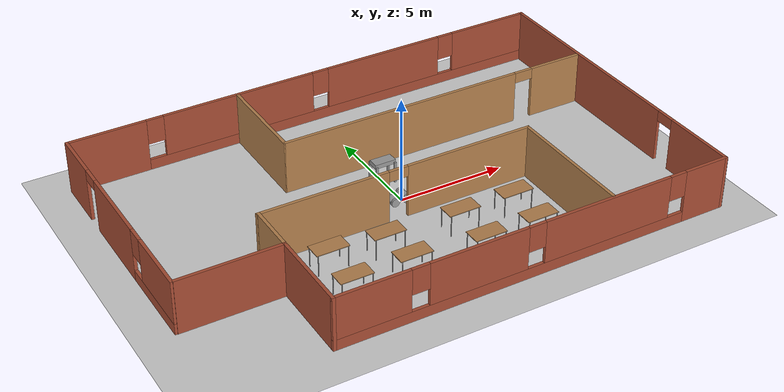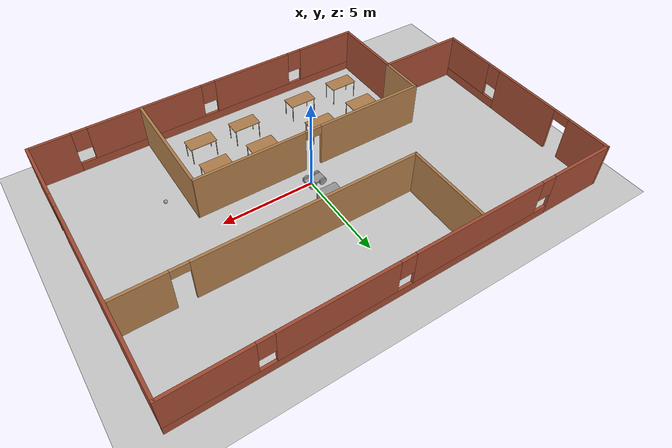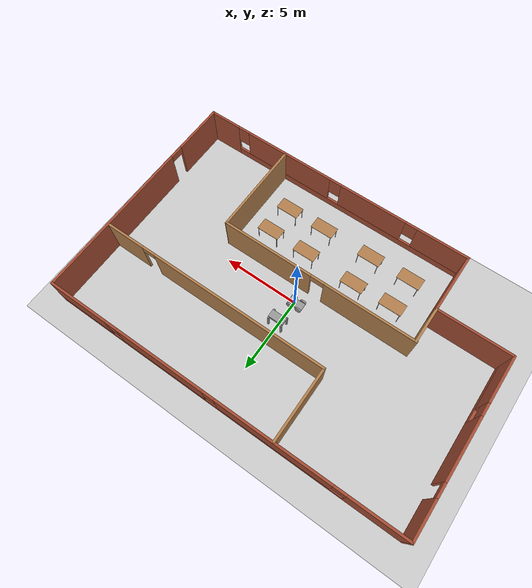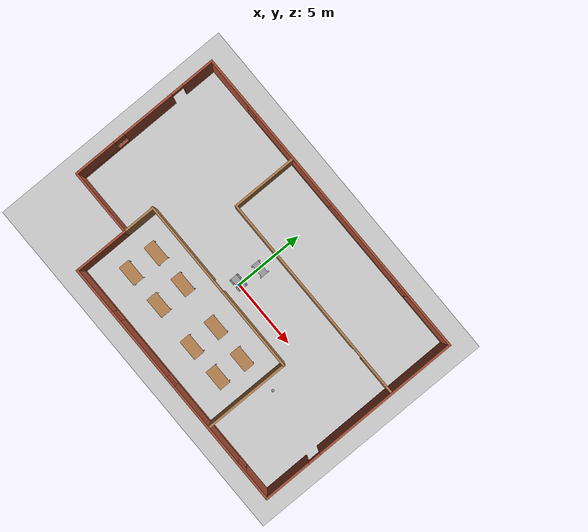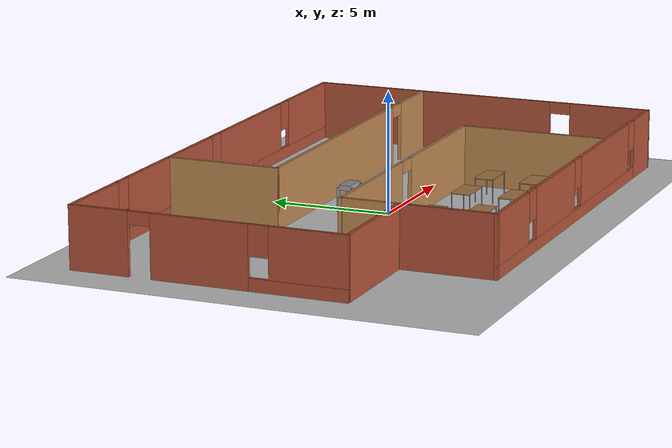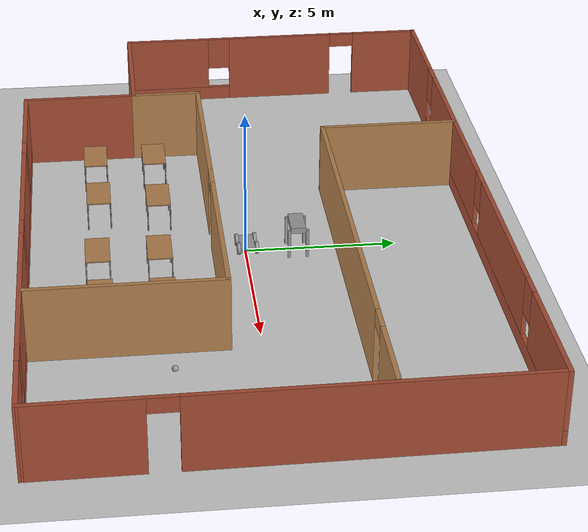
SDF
<sdf version="1.6">
 <world name="default">
  <plugin name="welcome_message" filename="libwelcome_message.so"/>
  <light name="sun" type="directional">
   <pose>0 0 10 0 -0 0</pose>
   <diffuse>0.8 0.8 0.8 1</diffuse>
   <specular>0.2 0.2 0.2 1</specular>
   <attenuation>
    <range>1000</range>
    <constant>0.9</constant>
    <linear>0.01</linear>
    <quadratic>0.001</quadratic>
   </attenuation>
   <direction>-0.5 0.1 -0.9</direction>
  </light>
  <model name="ground_plane">
   <static>1</static>
   <link name="link">
    <collision name="collision">
     <geometry><plane><normal>0 0 1</normal><size>100 100</size></plane></geometry>
     <surface><friction><ode><mu>100</mu><mu2>50</mu2></ode></friction></surface>
    </collision>
    <visual name="visual">
     <cast_shadows>0</cast_shadows>
     <geometry><plane><normal>0 0 1</normal><size>100 100</size></plane></geometry>
     <material>
      <script><uri>file://media/materials/scripts/gazebo.material</uri><name>Gazebo/Grey</name></script>
     </material>
    </visual>
   </link>
  </model>
  <gravity>0 0 -9.8</gravity>
  <magnetic_field>6e-06 2.3e-05 -4.2e-05</magnetic_field>
  <atmosphere type="adiabatic"/>
  <physics name="default_physics" default="0" type="ode">
   <max_step_size>0.001</max_step_size>
   <real_time_factor>1</real_time_factor>
   <real_time_update_rate>1000</real_time_update_rate>
  </physics>
  <scene><ambient>0.4 0.4 0.4 1</ambient><background>0.7 0.7 0.7 1</background><shadows>1</shadows></scene>
  <spherical_coordinates>
   <surface_model>EARTH_WGS84</surface_model>
   <latitude_deg>0</latitude_deg>
   <longitude_deg>0</longitude_deg>
   <elevation>0</elevation>
   <heading_deg>0</heading_deg>
  </spherical_coordinates>
  <model name="build2">
   <pose>-0.2148 0.30138 0 0 -0 0</pose>
   <link name="Wall_24">
    <pose>-11.6566 1.88746 0 0 0 -1.56954</pose>
    <visual name="Wall_24_Visual_0">
     <pose>-4.36296 0 1.25 0 -0 0</pose>
     <geometry><box><size>2.44005 0.15 2.5</size></box></geometry>
     <material>
      <script><uri>file://media/materials/scripts/gazebo.material</uri><name>Gazebo/Bricks</name></script>
      <ambient>1 1 1 1</ambient>
     </material>
     <meta><layer>0</layer></meta>
    </visual>
    <collision name="Wall_24_Collision_0">
     <geometry><box><size>2.44005 0.15 2.5</size></box></geometry>
     <pose>-4.36296 0 1.25 0 -0 0</pose>
    </collision>
    <visual name="Wall_24_Visual_1">
     <pose>-0.28088 0 1.25 0 -0 0</pose>
     <geometry><box><size>3.92411 0.15 2.5</size></box></geometry>
     <material>
      <script><uri>file://media/materials/scripts/gazebo.material</uri><name>Gazebo/Bricks</name></script>
      <ambient>1 1 1 1</ambient>
     </material>
     <meta><layer>0</layer></meta>
    </visual>
    <collision name="Wall_24_Collision_1">
     <geometry><box><size>3.92411 0.15 2.5</size></box></geometry>
     <pose>-0.28088 0 1.25 0 -0 0</pose>
    </collision>
    <visual name="Wall_24_Visual_2">
     <pose>3.63208 0 0.25 0 -0 0</pose>
     <geometry><box><size>3.90181 0.15 0.5</size></box></geometry>
     <material>
      <script><uri>file://media/materials/scripts/gazebo.material</uri><name>Gazebo/Bricks</name></script>
      <ambient>1 1 1 1</ambient>
     </material>
     <meta><layer>0</layer></meta>
    </visual>
    <collision name="Wall_24_Collision_2">
     <geometry><box><size>3.90181 0.15 0.5</size></box></geometry>
     <pose>3.63208 0 0.25 0 -0 0</pose>
    </collision>
    <visual name="Wall_24_Visual_3">
     <pose>4.03208 0 1.5 0 -0 0</pose>
     <geometry><box><size>3.10181 0.15 2</size></box></geometry>
     <material>
      <script><uri>file://media/materials/scripts/gazebo.material</uri><name>Gazebo/Bricks</name></script>
      <ambient>1 1 1 1</ambient>
     </material>
     <meta><layer>0</layer></meta>
    </visual>
    <collision name="Wall_24_Collision_3">
     <geometry><box><size>3.10181 0.15 2</size></box></geometry>
     <pose>4.03208 0 1.5 0 -0 0</pose>
    </collision>
    <visual name="Wall_24_Visual_4">
     <pose>2.08117 0 1.9 0 -0 0</pose>
     <geometry><box><size>0.8 0.15 1.2</size></box></geometry>
     <material>
      <script><uri>file://media/materials/scripts/gazebo.material</uri><name>Gazebo/Bricks</name></script>
      <ambient>1 1 1 1</ambient>
     </material>
     <meta><layer>0</layer></meta>
    </visual>
    <collision name="Wall_24_Collision_4">
     <geometry><box><size>0.8 0.15 1.2</size></box></geometry>
     <pose>2.08117 0 1.9 0 -0 0</pose>
    </collision>
    <visual name="Wall_24_Visual_5">
     <pose>-2.69294 0 2.25 0 -0 0</pose>
     <geometry><box><size>0.9 0.15 0.5</size></box></geometry>
     <material>
      <script><uri>file://media/materials/scripts/gazebo.material</uri><name>Gazebo/Bricks</name></script>
      <ambient>1 1 1 1</ambient>
     </material>
     <meta><layer>0</layer></meta>
    </visual>
    <collision name="Wall_24_Collision_5">
     <geometry><box><size>0.9 0.15 0.5</size></box></geometry>
     <pose>-2.69294 0 2.25 0 -0 0</pose>
    </collision>
   </link>
   <link name="Wall_26">
    <pose>-0.020877 7.44171 0 0 -0 0.003988</pose>
    <visual name="Wall_26_Visual_0">
     <pose>-9.86647 0 1.25 0 -0 0</pose>
     <geometry><box><size>3.62156 0.15 2.5</size></box></geometry>
     <material>
      <script><uri>file://media/materials/scripts/gazebo.material</uri><name>Gazebo/Bricks</name></script>
      <ambient>1 1 1 1</ambient>
     </material>
     <meta><layer>0</layer></meta>
    </visual>
    <collision name="Wall_26_Collision_0">
     <geometry><box><size>3.62156 0.15 2.5</size></box></geometry>
     <pose>-9.86647 0 1.25 0 -0 0</pose>
    </collision>
    <visual name="Wall_26_Visual_1">
     <pose>1.81078 0 0.25 0 -0 0</pose>
     <geometry><box><size>19.7329 0.15 0.5</size></box></geometry>
     <material>
      <script><uri>file://media/materials/scripts/gazebo.material</uri><name>Gazebo/Bricks</name></script>
      <ambient>1 1 1 1</ambient>
     </material>
     <meta><layer>0</layer></meta>
    </visual>
    <collision name="Wall_26_Collision_1">
     <geometry><box><size>19.7329 0.15 0.5</size></box></geometry>
     <pose>1.81078 0 0.25 0 -0 0</pose>
    </collision>
    <visual name="Wall_26_Visual_2">
     <pose>-3.58961 0 1.5 0 -0 0</pose>
     <geometry><box><size>7.33215 0.15 2</size></box></geometry>
     <material>
      <script><uri>file://media/materials/scripts/gazebo.material</uri><name>Gazebo/Bricks</name></script>
      <ambient>1 1 1 1</ambient>
     </material>
     <meta><layer>0</layer></meta>
    </visual>
    <collision name="Wall_26_Collision_2">
     <geometry><box><size>7.33215 0.15 2</size></box></geometry>
     <pose>-3.58961 0 1.5 0 -0 0</pose>
    </collision>
    <visual name="Wall_26_Visual_3">
     <pose>3.83417 0 1.5 0 -0 0</pose>
     <geometry><box><size>5.91541 0.15 2</size></box></geometry>
     <material>
      <script><uri>file://media/materials/scripts/gazebo.material</uri><name>Gazebo/Bricks</name></script>
      <ambient>1 1 1 1</ambient>
     </material>
     <meta><layer>0</layer></meta>
    </visual>
    <collision name="Wall_26_Collision_3">
     <geometry><box><size>5.91541 0.15 2</size></box></geometry>
     <pose>3.83417 0 1.5 0 -0 0</pose>
    </collision>
    <visual name="Wall_26_Visual_4">
     <pose>9.63456 0 1.5 0 -0 0</pose>
     <geometry><box><size>4.08537 0.15 2</size></box></geometry>
     <material>
      <script><uri>file://media/materials/scripts/gazebo.material</uri><name>Gazebo/Bricks</name></script>
      <ambient>1 1 1 1</ambient>
     </material>
     <meta><layer>0</layer></meta>
    </visual>
    <collision name="Wall_26_Collision_4">
     <geometry><box><size>4.08537 0.15 2</size></box></geometry>
     <pose>9.63456 0 1.5 0 -0 0</pose>
    </collision>
    <visual name="Wall_26_Visual_5">
     <pose>-7.65569 0 1.9 0 -0 0</pose>
     <geometry><box><size>0.8 0.15 1.2</size></box></geometry>
     <material>
      <script><uri>file://media/materials/scripts/gazebo.material</uri><name>Gazebo/Bricks</name></script>
      <ambient>1 1 1 1</ambient>
     </material>
     <meta><layer>0</layer></meta>
    </visual>
    <collision name="Wall_26_Collision_5">
     <geometry><box><size>0.8 0.15 1.2</size></box></geometry>
     <pose>-7.65569 0 1.9 0 -0 0</pose>
    </collision>
    <visual name="Wall_26_Visual_6">
     <pose>0.476465 0 1.9 0 -0 0</pose>
     <geometry><box><size>0.8 0.15 1.2</size></box></geometry>
     <material>
      <script><uri>file://media/materials/scripts/gazebo.material</uri><name>Gazebo/Bricks</name></script>
      <ambient>1 1 1 1</ambient>
     </material>
     <meta><layer>0</layer></meta>
    </visual>
    <collision name="Wall_26_Collision_6">
     <geometry><box><size>0.8 0.15 1.2</size></box></geometry>
     <pose>0.476465 0 1.9 0 -0 0</pose>
    </collision>
    <visual name="Wall_26_Visual_7">
     <pose>7.19188 0 1.9 0 -0 0</pose>
     <geometry><box><size>0.8 0.15 1.2</size></box></geometry>
     <material>
      <script><uri>file://media/materials/scripts/gazebo.material</uri><name>Gazebo/Bricks</name></script>
      <ambient>1 1 1 1</ambient>
     </material>
     <meta><layer>0</layer></meta>
    </visual>
    <collision name="Wall_26_Collision_7">
     <geometry><box><size>0.8 0.15 1.2</size></box></geometry>
     <pose>7.19188 0 1.9 0 -0 0</pose>
    </collision>
   </link>
   <link name="Wall_27">
    <pose>11.6222 -0.019992 0 0 0 -1.56531</pose>
    <visual name="Wall_27_Visual_0">
     <pose>-2.21048 0 1.25 0 -0 0</pose>
     <geometry><box><size>10.665 0.15 2.5</size></box></geometry>
     <material>
      <script><uri>file://media/materials/scripts/gazebo.material</uri><name>Gazebo/Bricks</name></script>
      <ambient>1 1 1 1</ambient>
     </material>
     <meta><layer>0</layer></meta>
    </visual>
    <collision name="Wall_27_Collision_0">
     <geometry><box><size>10.665 0.15 2.5</size></box></geometry>
     <pose>-2.21048 0 1.25 0 -0 0</pose>
    </collision>
    <visual name="Wall_27_Visual_1">
     <pose>5.78251 0 1.25 0 -0 0</pose>
     <geometry><box><size>3.52096 0.15 2.5</size></box></geometry>
     <material>
      <script><uri>file://media/materials/scripts/gazebo.material</uri><name>Gazebo/Bricks</name></script>
      <ambient>1 1 1 1</ambient>
     </material>
     <meta><layer>0</layer></meta>
    </visual>
    <collision name="Wall_27_Collision_1">
     <geometry><box><size>3.52096 0.15 2.5</size></box></geometry>
     <pose>5.78251 0 1.25 0 -0 0</pose>
    </collision>
    <visual name="Wall_27_Visual_2">
     <pose>3.57203 0 2.25 0 -0 0</pose>
     <geometry><box><size>0.9 0.15 0.5</size></box></geometry>
     <material>
      <script><uri>file://media/materials/scripts/gazebo.material</uri><name>Gazebo/Bricks</name></script>
      <ambient>1 1 1 1</ambient>
     </material>
     <meta><layer>0</layer></meta>
    </visual>
    <collision name="Wall_27_Collision_2">
     <geometry><box><size>0.9 0.15 0.5</size></box></geometry>
     <pose>3.57203 0 2.25 0 -0 0</pose>
    </collision>
   </link>
   <link name="Wall_28">
    <pose>2.36317 -7.48751 0 0 -0 3.14159</pose>
    <visual name="Wall_28_Visual_0">
     <pose>-8.2825 0 1.25 0 -0 0</pose>
     <geometry><box><size>2.18499 0.15 2.5</size></box></geometry>
     <material>
      <script><uri>file://media/materials/scripts/gazebo.material</uri><name>Gazebo/Bricks</name></script>
      <ambient>1 1 1 1</ambient>
     </material>
     <meta><layer>0</layer></meta>
    </visual>
    <collision name="Wall_28_Collision_0">
     <geometry><box><size>2.18499 0.15 2.5</size></box></geometry>
     <pose>-8.2825 0 1.25 0 -0 0</pose>
    </collision>
    <visual name="Wall_28_Visual_1">
     <pose>1.0925 0 0.25 0 -0 0</pose>
     <geometry><box><size>16.565 0.15 0.5</size></box></geometry>
     <material>
      <script><uri>file://media/materials/scripts/gazebo.material</uri><name>Gazebo/Bricks</name></script>
      <ambient>1 1 1 1</ambient>
     </material>
     <meta><layer>0</layer></meta>
    </visual>
    <collision name="Wall_28_Collision_1">
     <geometry><box><size>16.565 0.15 0.5</size></box></geometry>
     <pose>1.0925 0 0.25 0 -0 0</pose>
    </collision>
    <visual name="Wall_28_Visual_2">
     <pose>-3.2906 0 1.5 0 -0 0</pose>
     <geometry><box><size>6.19881 0.15 2</size></box></geometry>
     <material>
      <script><uri>file://media/materials/scripts/gazebo.material</uri><name>Gazebo/Bricks</name></script>
      <ambient>1 1 1 1</ambient>
     </material>
     <meta><layer>0</layer></meta>
    </visual>
    <collision name="Wall_28_Collision_2">
     <geometry><box><size>6.19881 0.15 2</size></box></geometry>
     <pose>-3.2906 0 1.5 0 -0 0</pose>
    </collision>
    <visual name="Wall_28_Visual_3">
     <pose>2.87888 0 1.5 0 -0 0</pose>
     <geometry><box><size>4.54014 0.15 2</size></box></geometry>
     <material>
      <script><uri>file://media/materials/scripts/gazebo.material</uri><name>Gazebo/Bricks</name></script>
      <ambient>1 1 1 1</ambient>
     </material>
     <meta><layer>0</layer></meta>
    </visual>
    <collision name="Wall_28_Collision_3">
     <geometry><box><size>4.54014 0.15 2</size></box></geometry>
     <pose>2.87888 0 1.5 0 -0 0</pose>
    </collision>
    <visual name="Wall_28_Visual_4">
     <pose>7.66197 0 1.5 0 -0 0</pose>
     <geometry><box><size>3.42605 0.15 2</size></box></geometry>
     <material>
      <script><uri>file://media/materials/scripts/gazebo.material</uri><name>Gazebo/Bricks</name></script>
      <ambient>1 1 1 1</ambient>
     </material>
     <meta><layer>0</layer></meta>
    </visual>
    <collision name="Wall_28_Collision_4">
     <geometry><box><size>3.42605 0.15 2</size></box></geometry>
     <pose>7.66197 0 1.5 0 -0 0</pose>
    </collision>
    <visual name="Wall_28_Visual_5">
     <pose>-6.79001 0 1.9 0 -0 0</pose>
     <geometry><box><size>0.8 0.15 1.2</size></box></geometry>
     <material>
      <script><uri>file://media/materials/scripts/gazebo.material</uri><name>Gazebo/Bricks</name></script>
      <ambient>1 1 1 1</ambient>
     </material>
     <meta><layer>0</layer></meta>
    </visual>
    <collision name="Wall_28_Collision_5">
     <geometry><box><size>0.8 0.15 1.2</size></box></geometry>
     <pose>-6.79001 0 1.9 0 -0 0</pose>
    </collision>
    <visual name="Wall_28_Visual_6">
     <pose>0.208809 0 1.9 0 -0 0</pose>
     <geometry><box><size>0.8 0.15 1.2</size></box></geometry>
     <material>
      <script><uri>file://media/materials/scripts/gazebo.material</uri><name>Gazebo/Bricks</name></script>
      <ambient>1 1 1 1</ambient>
     </material>
     <meta><layer>0</layer></meta>
    </visual>
    <collision name="Wall_28_Collision_6">
     <geometry><box><size>0.8 0.15 1.2</size></box></geometry>
     <pose>0.208809 0 1.9 0 -0 0</pose>
    </collision>
    <visual name="Wall_28_Visual_7">
     <pose>5.54894 0 1.9 0 -0 0</pose>
     <geometry><box><size>0.8 0.15 1.2</size></box></geometry>
     <material>
      <script><uri>file://media/materials/scripts/gazebo.material</uri><name>Gazebo/Bricks</name></script>
      <ambient>1 1 1 1</ambient>
     </material>
     <meta><layer>0</layer></meta>
    </visual>
    <collision name="Wall_28_Collision_7">
     <geometry><box><size>0.8 0.15 1.2</size></box></geometry>
     <pose>5.54894 0 1.9 0 -0 0</pose>
    </collision>
   </link>
   <link name="Wall_29">
    <collision name="Wall_29_Collision">
     <geometry><box><size>4 0.15 2.5</size></box></geometry>
     <pose>0 0 1.25 0 -0 0</pose>
    </collision>
    <visual name="Wall_29_Visual">
     <pose>0 0 1.25 0 -0 0</pose>
     <geometry><box><size>4 0.15 2.5</size></box></geometry>
     <material>
      <script><uri>file://media/materials/scripts/gazebo.material</uri><name>Gazebo/Bricks</name></script>
      <ambient>1 1 1 1</ambient>
     </material>
     <meta><layer>0</layer></meta>
    </visual>
    <pose>-6.93683 -5.56251 0 0 -0 1.5708</pose>
   </link>
   <link name="Wall_31">
    <collision name="Wall_31_Collision">
     <geometry><box><size>4.75 0.15 2.5</size></box></geometry>
     <pose>0 0 1.25 0 -0 0</pose>
    </collision>
    <visual name="Wall_31_Visual">
     <pose>0 0 1.25 0 -0 0</pose>
     <geometry><box><size>4.75 0.15 2.5</size></box></geometry>
     <material>
      <script><uri>file://media/materials/scripts/gazebo.material</uri><name>Gazebo/Bricks</name></script>
      <ambient>1 1 1 1</ambient>
     </material>
     <meta><layer>0</layer></meta>
    </visual>
    <pose>-9.23683 -3.63751 0 0 -0 3.14159</pose>
   </link>
   <link name="Wall_33">
    <collision name="Wall_33_Collision">
     <geometry><box><size>2.44839 0.15 2.5</size></box></geometry>
     <pose>0 0 1.25 0 -0 0</pose>
    </collision>
    <visual name="Wall_33_Visual">
     <pose>0 0 1.25 0 -0 0</pose>
     <geometry><box><size>2.44839 0.15 2.5</size></box></geometry>
     <material>
      <script><uri>file://media/materials/scripts/gazebo.material</uri><name>Gazebo/Wood</name></script>
      <ambient>1 1 1 1</ambient>
     </material>
     <meta><layer>0</layer></meta>
    </visual>
    <pose>-6.93683 -2.48832 0 0 -0 1.5708</pose>
   </link>
   <link name="Wall_34">
    <pose>-0.547009 -1.33912 0 0 -0 0</pose>
    <visual name="Wall_34_Visual_0">
     <pose>-3.47958 0 1.25 0 -0 0</pose>
     <geometry><box><size>6.04085 0.15 2.5</size></box></geometry>
     <material>
      <script><uri>file://media/materials/scripts/gazebo.material</uri><name>Gazebo/Wood</name></script>
      <ambient>1 1 1 1</ambient>
     </material>
     <meta><layer>0</layer></meta>
    </visual>
    <collision name="Wall_34_Collision_0">
     <geometry><box><size>6.04085 0.15 2.5</size></box></geometry>
     <pose>-3.47958 0 1.25 0 -0 0</pose>
    </collision>
    <visual name="Wall_34_Visual_1">
     <pose>3.47042 0 1.25 0 -0 0</pose>
     <geometry><box><size>6.05915 0.15 2.5</size></box></geometry>
     <material>
      <script><uri>file://media/materials/scripts/gazebo.material</uri><name>Gazebo/Wood</name></script>
      <ambient>1 1 1 1</ambient>
     </material>
     <meta><layer>0</layer></meta>
    </visual>
    <collision name="Wall_34_Collision_1">
     <geometry><box><size>6.05915 0.15 2.5</size></box></geometry>
     <pose>3.47042 0 1.25 0 -0 0</pose>
    </collision>
    <visual name="Wall_34_Visual_2">
     <pose>-0.009154 0 2.25 0 -0 0</pose>
     <geometry><box><size>0.9 0.15 0.5</size></box></geometry>
     <material>
      <script><uri>file://media/materials/scripts/gazebo.material</uri><name>Gazebo/Wood</name></script>
      <ambient>1 1 1 1</ambient>
     </material>
     <meta><layer>0</layer></meta>
    </visual>
    <collision name="Wall_34_Collision_2">
     <geometry><box><size>0.9 0.15 0.5</size></box></geometry>
     <pose>-0.009154 0 2.25 0 -0 0</pose>
    </collision>
   </link>
   <link name="Wall_35">
    <collision name="Wall_35_Collision">
     <geometry><box><size>6.19839 0.15 2.5</size></box></geometry>
     <pose>0 0 1.25 0 -0 0</pose>
    </collision>
    <visual name="Wall_35_Visual">
     <pose>0 0 1.25 0 -0 0</pose>
     <geometry><box><size>6.19839 0.15 2.5</size></box></geometry>
     <material>
      <script><uri>file://media/materials/scripts/gazebo.material</uri><name>Gazebo/Wood</name></script>
      <ambient>1 1 1 1</ambient>
     </material>
     <meta><layer>0</layer></meta>
    </visual>
    <pose>5.91317 -4.36332 0 0 0 -1.5708</pose>
   </link>
   <link name="Wall_37">
    <collision name="Wall_37_Collision">
     <geometry><box><size>4.75 0.15 2.5</size></box></geometry>
     <pose>0 0 1.25 0 -0 0</pose>
    </collision>
    <visual name="Wall_37_Visual">
     <pose>0 0 1.25 0 -0 0</pose>
     <geometry><box><size>4.75 0.15 2.5</size></box></geometry>
     <material>
      <script><uri>file://media/materials/scripts/gazebo.material</uri><name>Gazebo/Wood</name></script>
      <ambient>1 1 1 1</ambient>
     </material>
     <meta><layer>0</layer></meta>
    </visual>
    <pose>-3.69922 5.07164 0 0 0 -1.5708</pose>
   </link>
   <link name="Wall_38">
    <pose>3.89123 2.77164 0 0 -0 0</pose>
    <visual name="Wall_38_Visual_0">
     <pose>-1.7504 0 1.25 0 -0 0</pose>
     <geometry><box><size>11.7492 0.15 2.5</size></box></geometry>
     <material>
      <script><uri>file://media/materials/scripts/gazebo.material</uri><name>Gazebo/Wood</name></script>
      <ambient>1 1 1 1</ambient>
     </material>
     <meta><layer>0</layer></meta>
    </visual>
    <collision name="Wall_38_Collision_0">
     <geometry><box><size>11.7492 0.15 2.5</size></box></geometry>
     <pose>-1.7504 0 1.25 0 -0 0</pose>
    </collision>
    <visual name="Wall_38_Visual_1">
     <pose>6.3246 0 1.25 0 -0 0</pose>
     <geometry><box><size>2.6008 0.15 2.5</size></box></geometry>
     <material>
      <script><uri>file://media/materials/scripts/gazebo.material</uri><name>Gazebo/Wood</name></script>
      <ambient>1 1 1 1</ambient>
     </material>
     <meta><layer>0</layer></meta>
    </visual>
    <collision name="Wall_38_Collision_1">
     <geometry><box><size>2.6008 0.15 2.5</size></box></geometry>
     <pose>6.3246 0 1.25 0 -0 0</pose>
    </collision>
    <visual name="Wall_38_Visual_2">
     <pose>4.5742 0 2.25 0 -0 0</pose>
     <geometry><box><size>0.9 0.15 0.5</size></box></geometry>
     <material>
      <script><uri>file://media/materials/scripts/gazebo.material</uri><name>Gazebo/Wood</name></script>
      <ambient>1 1 1 1</ambient>
     </material>
     <meta><layer>0</layer></meta>
    </visual>
    <collision name="Wall_38_Collision_2">
     <geometry><box><size>0.9 0.15 0.5</size></box></geometry>
     <pose>4.5742 0 2.25 0 -0 0</pose>
    </collision>
   </link>
   <static>1</static>
  </model>
  <model name="table">
   <static>1</static>
   <link name="link">
    <collision name="surface">
     <pose>0 0 1 0 -0 0</pose>
     <geometry><box><size>1.5 0.8 0.03</size></box></geometry>
     <surface><friction><ode><mu>0.6</mu><mu2>0.6</mu2></ode></friction></surface>
    </collision>
    <visual name="visual1">
     <pose>0 0 1 0 -0 0</pose>
     <geometry><box><size>1.5 0.8 0.03</size></box></geometry>
     <material>
      <script><uri>file://media/materials/scripts/gazebo.material</uri><name>Gazebo/Wood</name></script>
     </material>
    </visual>
    <collision name="front_left_leg">
     <pose>0.68 0.38 0.5 0 -0 0</pose>
     <geometry><cylinder><radius>0.02</radius><length>1</length></cylinder></geometry>
    </collision>
    <visual name="front_left_leg">
     <pose>0.68 0.38 0.5 0 -0 0</pose>
     <geometry><cylinder><radius>0.02</radius><length>1</length></cylinder></geometry>
     <material>
      <script><uri>file://media/materials/scripts/gazebo.material</uri><name>Gazebo/Grey</name></script>
     </material>
    </visual>
    <collision name="front_right_leg">
     <pose>0.68 -0.38 0.5 0 -0 0</pose>
     <geometry><cylinder><radius>0.02</radius><length>1</length></cylinder></geometry>
    </collision>
    <visual name="front_right_leg">
     <pose>0.68 -0.38 0.5 0 -0 0</pose>
     <geometry><cylinder><radius>0.02</radius><length>1</length></cylinder></geometry>
     <material>
      <script><uri>file://media/materials/scripts/gazebo.material</uri><name>Gazebo/Grey</name></script>
     </material>
    </visual>
    <collision name="back_right_leg">
     <pose>-0.68 -0.38 0.5 0 -0 0</pose>
     <geometry><cylinder><radius>0.02</radius><length>1</length></cylinder></geometry>
    </collision>
    <visual name="back_right_leg">
     <pose>-0.68 -0.38 0.5 0 -0 0</pose>
     <geometry><cylinder><radius>0.02</radius><length>1</length></cylinder></geometry>
     <material>
      <script><uri>file://media/materials/scripts/gazebo.material</uri><name>Gazebo/Grey</name></script>
     </material>
    </visual>
    <collision name="back_left_leg">
     <pose>-0.68 0.38 0.5 0 -0 0</pose>
     <geometry><cylinder><radius>0.02</radius><length>1</length></cylinder></geometry>
    </collision>
    <visual name="back_left_leg">
     <pose>-0.68 0.38 0.5 0 -0 0</pose>
     <geometry><cylinder><radius>0.02</radius><length>1</length></cylinder></geometry>
     <material>
      <script><uri>file://media/materials/scripts/gazebo.material</uri><name>Gazebo/Grey</name></script>
     </material>
    </visual>
   </link>
   <pose>3.69485 -4.8392 0 0 -0 0</pose>
  </model>
  <model name="table_0">
   <static>1</static>
   <link name="link">
    <collision name="surface">
     <pose>0 0 1 0 -0 0</pose>
     <geometry><box><size>1.5 0.8 0.03</size></box></geometry>
     <surface><friction><ode><mu>0.6</mu><mu2>0.6</mu2></ode></friction></surface>
    </collision>
    <visual name="visual1">
     <pose>0 0 1 0 -0 0</pose>
     <geometry><box><size>1.5 0.8 0.03</size></box></geometry>
     <material>
      <script><uri>file://media/materials/scripts/gazebo.material</uri><name>Gazebo/Wood</name></script>
     </material>
    </visual>
    <collision name="front_left_leg">
     <pose>0.68 0.38 0.5 0 -0 0</pose>
     <geometry><cylinder><radius>0.02</radius><length>1</length></cylinder></geometry>
    </collision>
    <visual name="front_left_leg">
     <pose>0.68 0.38 0.5 0 -0 0</pose>
     <geometry><cylinder><radius>0.02</radius><length>1</length></cylinder></geometry>
     <material>
      <script><uri>file://media/materials/scripts/gazebo.material</uri><name>Gazebo/Grey</name></script>
     </material>
    </visual>
    <collision name="front_right_leg">
     <pose>0.68 -0.38 0.5 0 -0 0</pose>
     <geometry><cylinder><radius>0.02</radius><length>1</length></cylinder></geometry>
    </collision>
    <visual name="front_right_leg">
     <pose>0.68 -0.38 0.5 0 -0 0</pose>
     <geometry><cylinder><radius>0.02</radius><length>1</length></cylinder></geometry>
     <material>
      <script><uri>file://media/materials/scripts/gazebo.material</uri><name>Gazebo/Grey</name></script>
     </material>
    </visual>
    <collision name="back_right_leg">
     <pose>-0.68 -0.38 0.5 0 -0 0</pose>
     <geometry><cylinder><radius>0.02</radius><length>1</length></cylinder></geometry>
    </collision>
    <visual name="back_right_leg">
     <pose>-0.68 -0.38 0.5 0 -0 0</pose>
     <geometry><cylinder><radius>0.02</radius><length>1</length></cylinder></geometry>
     <material>
      <script><uri>file://media/materials/scripts/gazebo.material</uri><name>Gazebo/Grey</name></script>
     </material>
    </visual>
    <collision name="back_left_leg">
     <pose>-0.68 0.38 0.5 0 -0 0</pose>
     <geometry><cylinder><radius>0.02</radius><length>1</length></cylinder></geometry>
    </collision>
    <visual name="back_left_leg">
     <pose>-0.68 0.38 0.5 0 -0 0</pose>
     <geometry><cylinder><radius>0.02</radius><length>1</length></cylinder></geometry>
     <material>
      <script><uri>file://media/materials/scripts/gazebo.material</uri><name>Gazebo/Grey</name></script>
     </material>
    </visual>
   </link>
   <pose>3.78546 -2.89544 0 0 -0 0</pose>
  </model>
  <model name="table_1">
   <static>1</static>
   <link name="link">
    <collision name="surface">
     <pose>0 0 1 0 -0 0</pose>
     <geometry><box><size>1.5 0.8 0.03</size></box></geometry>
     <surface><friction><ode><mu>0.6</mu><mu2>0.6</mu2></ode></friction></surface>
    </collision>
    <visual name="visual1">
     <pose>0 0 1 0 -0 0</pose>
     <geometry><box><size>1.5 0.8 0.03</size></box></geometry>
     <material>
      <script><uri>file://media/materials/scripts/gazebo.material</uri><name>Gazebo/Wood</name></script>
     </material>
    </visual>
    <collision name="front_left_leg">
     <pose>0.68 0.38 0.5 0 -0 0</pose>
     <geometry><cylinder><radius>0.02</radius><length>1</length></cylinder></geometry>
    </collision>
    <visual name="front_left_leg">
     <pose>0.68 0.38 0.5 0 -0 0</pose>
     <geometry><cylinder><radius>0.02</radius><length>1</length></cylinder></geometry>
     <material>
      <script><uri>file://media/materials/scripts/gazebo.material</uri><name>Gazebo/Grey</name></script>
     </material>
    </visual>
    <collision name="front_right_leg">
     <pose>0.68 -0.38 0.5 0 -0 0</pose>
     <geometry><cylinder><radius>0.02</radius><length>1</length></cylinder></geometry>
    </collision>
    <visual name="front_right_leg">
     <pose>0.68 -0.38 0.5 0 -0 0</pose>
     <geometry><cylinder><radius>0.02</radius><length>1</length></cylinder></geometry>
     <material>
      <script><uri>file://media/materials/scripts/gazebo.material</uri><name>Gazebo/Grey</name></script>
     </material>
    </visual>
    <collision name="back_right_leg">
     <pose>-0.68 -0.38 0.5 0 -0 0</pose>
     <geometry><cylinder><radius>0.02</radius><length>1</length></cylinder></geometry>
    </collision>
    <visual name="back_right_leg">
     <pose>-0.68 -0.38 0.5 0 -0 0</pose>
     <geometry><cylinder><radius>0.02</radius><length>1</length></cylinder></geometry>
     <material>
      <script><uri>file://media/materials/scripts/gazebo.material</uri><name>Gazebo/Grey</name></script>
     </material>
    </visual>
    <collision name="back_left_leg">
     <pose>-0.68 0.38 0.5 0 -0 0</pose>
     <geometry><cylinder><radius>0.02</radius><length>1</length></cylinder></geometry>
    </collision>
    <visual name="back_left_leg">
     <pose>-0.68 0.38 0.5 0 -0 0</pose>
     <geometry><cylinder><radius>0.02</radius><length>1</length></cylinder></geometry>
     <material>
      <script><uri>file://media/materials/scripts/gazebo.material</uri><name>Gazebo/Grey</name></script>
     </material>
    </visual>
   </link>
   <pose>1.13201 -4.88158 0 0 -0 0</pose>
  </model>
  <model name="table_2">
   <static>1</static>
   <link name="link">
    <collision name="surface">
     <pose>0 0 1 0 -0 0</pose>
     <geometry><box><size>1.5 0.8 0.03</size></box></geometry>
     <surface><friction><ode><mu>0.6</mu><mu2>0.6</mu2></ode></friction></surface>
    </collision>
    <visual name="visual1">
     <pose>0 0 1 0 -0 0</pose>
     <geometry><box><size>1.5 0.8 0.03</size></box></geometry>
     <material>
      <script><uri>file://media/materials/scripts/gazebo.material</uri><name>Gazebo/Wood</name></script>
     </material>
    </visual>
    <collision name="front_left_leg">
     <pose>0.68 0.38 0.5 0 -0 0</pose>
     <geometry><cylinder><radius>0.02</radius><length>1</length></cylinder></geometry>
    </collision>
    <visual name="front_left_leg">
     <pose>0.68 0.38 0.5 0 -0 0</pose>
     <geometry><cylinder><radius>0.02</radius><length>1</length></cylinder></geometry>
     <material>
      <script><uri>file://media/materials/scripts/gazebo.material</uri><name>Gazebo/Grey</name></script>
     </material>
    </visual>
    <collision name="front_right_leg">
     <pose>0.68 -0.38 0.5 0 -0 0</pose>
     <geometry><cylinder><radius>0.02</radius><length>1</length></cylinder></geometry>
    </collision>
    <visual name="front_right_leg">
     <pose>0.68 -0.38 0.5 0 -0 0</pose>
     <geometry><cylinder><radius>0.02</radius><length>1</length></cylinder></geometry>
     <material>
      <script><uri>file://media/materials/scripts/gazebo.material</uri><name>Gazebo/Grey</name></script>
     </material>
    </visual>
    <collision name="back_right_leg">
     <pose>-0.68 -0.38 0.5 0 -0 0</pose>
     <geometry><cylinder><radius>0.02</radius><length>1</length></cylinder></geometry>
    </collision>
    <visual name="back_right_leg">
     <pose>-0.68 -0.38 0.5 0 -0 0</pose>
     <geometry><cylinder><radius>0.02</radius><length>1</length></cylinder></geometry>
     <material>
      <script><uri>file://media/materials/scripts/gazebo.material</uri><name>Gazebo/Grey</name></script>
     </material>
    </visual>
    <collision name="back_left_leg">
     <pose>-0.68 0.38 0.5 0 -0 0</pose>
     <geometry><cylinder><radius>0.02</radius><length>1</length></cylinder></geometry>
    </collision>
    <visual name="back_left_leg">
     <pose>-0.68 0.38 0.5 0 -0 0</pose>
     <geometry><cylinder><radius>0.02</radius><length>1</length></cylinder></geometry>
     <material>
      <script><uri>file://media/materials/scripts/gazebo.material</uri><name>Gazebo/Grey</name></script>
     </material>
    </visual>
   </link>
   <pose>1.14087 -2.89178 0 0 -0 0</pose>
  </model>
  <model name="table_2_clone">
   <static>1</static>
   <link name="link">
    <collision name="surface">
     <pose>0 0 1 0 -0 0</pose>
     <geometry><box><size>1.5 0.8 0.03</size></box></geometry>
     <surface><friction><ode><mu>0.6</mu><mu2>0.6</mu2></ode></friction></surface>
    </collision>
    <visual name="visual1">
     <pose>0 0 1 0 -0 0</pose>
     <geometry><box><size>1.5 0.8 0.03</size></box></geometry>
     <material>
      <script><uri>file://media/materials/scripts/gazebo.material</uri><name>Gazebo/Wood</name></script>
     </material>
    </visual>
    <collision name="front_left_leg">
     <pose>0.68 0.38 0.5 0 -0 0</pose>
     <geometry><cylinder><radius>0.02</radius><length>1</length></cylinder></geometry>
    </collision>
    <visual name="front_left_leg">
     <pose>0.68 0.38 0.5 0 -0 0</pose>
     <geometry><cylinder><radius>0.02</radius><length>1</length></cylinder></geometry>
     <material>
      <script><uri>file://media/materials/scripts/gazebo.material</uri><name>Gazebo/Grey</name></script>
     </material>
    </visual>
    <collision name="front_right_leg">
     <pose>0.68 -0.38 0.5 0 -0 0</pose>
     <geometry><cylinder><radius>0.02</radius><length>1</length></cylinder></geometry>
    </collision>
    <visual name="front_right_leg">
     <pose>0.68 -0.38 0.5 0 -0 0</pose>
     <geometry><cylinder><radius>0.02</radius><length>1</length></cylinder></geometry>
     <material>
      <script><uri>file://media/materials/scripts/gazebo.material</uri><name>Gazebo/Grey</name></script>
     </material>
    </visual>
    <collision name="back_right_leg">
     <pose>-0.68 -0.38 0.5 0 -0 0</pose>
     <geometry><cylinder><radius>0.02</radius><length>1</length></cylinder></geometry>
    </collision>
    <visual name="back_right_leg">
     <pose>-0.68 -0.38 0.5 0 -0 0</pose>
     <geometry><cylinder><radius>0.02</radius><length>1</length></cylinder></geometry>
     <material>
      <script><uri>file://media/materials/scripts/gazebo.material</uri><name>Gazebo/Grey</name></script>
     </material>
    </visual>
    <collision name="back_left_leg">
     <pose>-0.68 0.38 0.5 0 -0 0</pose>
     <geometry><cylinder><radius>0.02</radius><length>1</length></cylinder></geometry>
    </collision>
    <visual name="back_left_leg">
     <pose>-0.68 0.38 0.5 0 -0 0</pose>
     <geometry><cylinder><radius>0.02</radius><length>1</length></cylinder></geometry>
     <material>
      <script><uri>file://media/materials/scripts/gazebo.material</uri><name>Gazebo/Grey</name></script>
     </material>
    </visual>
   </link>
   <pose>-2.34773 -2.76218 0 0 -0 0</pose>
  </model>
  <model name="table_2_clone_0">
   <static>1</static>
   <link name="link">
    <collision name="surface">
     <pose>0 0 1 0 -0 0</pose>
     <geometry><box><size>1.5 0.8 0.03</size></box></geometry>
     <surface><friction><ode><mu>0.6</mu><mu2>0.6</mu2></ode></friction></surface>
    </collision>
    <visual name="visual1">
     <pose>0 0 1 0 -0 0</pose>
     <geometry><box><size>1.5 0.8 0.03</size></box></geometry>
     <material>
      <script><uri>file://media/materials/scripts/gazebo.material</uri><name>Gazebo/Wood</name></script>
     </material>
    </visual>
    <collision name="front_left_leg">
     <pose>0.68 0.38 0.5 0 -0 0</pose>
     <geometry><cylinder><radius>0.02</radius><length>1</length></cylinder></geometry>
    </collision>
    <visual name="front_left_leg">
     <pose>0.68 0.38 0.5 0 -0 0</pose>
     <geometry><cylinder><radius>0.02</radius><length>1</length></cylinder></geometry>
     <material>
      <script><uri>file://media/materials/scripts/gazebo.material</uri><name>Gazebo/Grey</name></script>
     </material>
    </visual>
    <collision name="front_right_leg">
     <pose>0.68 -0.38 0.5 0 -0 0</pose>
     <geometry><cylinder><radius>0.02</radius><length>1</length></cylinder></geometry>
    </collision>
    <visual name="front_right_leg">
     <pose>0.68 -0.38 0.5 0 -0 0</pose>
     <geometry><cylinder><radius>0.02</radius><length>1</length></cylinder></geometry>
     <material>
      <script><uri>file://media/materials/scripts/gazebo.material</uri><name>Gazebo/Grey</name></script>
     </material>
    </visual>
    <collision name="back_right_leg">
     <pose>-0.68 -0.38 0.5 0 -0 0</pose>
     <geometry><cylinder><radius>0.02</radius><length>1</length></cylinder></geometry>
    </collision>
    <visual name="back_right_leg">
     <pose>-0.68 -0.38 0.5 0 -0 0</pose>
     <geometry><cylinder><radius>0.02</radius><length>1</length></cylinder></geometry>
     <material>
      <script><uri>file://media/materials/scripts/gazebo.material</uri><name>Gazebo/Grey</name></script>
     </material>
    </visual>
    <collision name="back_left_leg">
     <pose>-0.68 0.38 0.5 0 -0 0</pose>
     <geometry><cylinder><radius>0.02</radius><length>1</length></cylinder></geometry>
    </collision>
    <visual name="back_left_leg">
     <pose>-0.68 0.38 0.5 0 -0 0</pose>
     <geometry><cylinder><radius>0.02</radius><length>1</length></cylinder></geometry>
     <material>
      <script><uri>file://media/materials/scripts/gazebo.material</uri><name>Gazebo/Grey</name></script>
     </material>
    </visual>
   </link>
   <pose>-2.29644 -4.76525 0.200823 0 -0 0</pose>
  </model>
  <model name="table_2_clone_0_clone">
   <static>1</static>
   <link name="link">
    <collision name="surface">
     <pose>0 0 1 0 -0 0</pose>
     <geometry><box><size>1.5 0.8 0.03</size></box></geometry>
     <surface><friction><ode><mu>0.6</mu><mu2>0.6</mu2></ode></friction></surface>
    </collision>
    <visual name="visual1">
     <pose>0 0 1 0 -0 0</pose>
     <geometry><box><size>1.5 0.8 0.03</size></box></geometry>
     <material>
      <script><uri>file://media/materials/scripts/gazebo.material</uri><name>Gazebo/Wood</name></script>
     </material>
    </visual>
    <collision name="front_left_leg">
     <pose>0.68 0.38 0.5 0 -0 0</pose>
     <geometry><cylinder><radius>0.02</radius><length>1</length></cylinder></geometry>
    </collision>
    <visual name="front_left_leg">
     <pose>0.68 0.38 0.5 0 -0 0</pose>
     <geometry><cylinder><radius>0.02</radius><length>1</length></cylinder></geometry>
     <material>
      <script><uri>file://media/materials/scripts/gazebo.material</uri><name>Gazebo/Grey</name></script>
     </material>
    </visual>
    <collision name="front_right_leg">
     <pose>0.68 -0.38 0.5 0 -0 0</pose>
     <geometry><cylinder><radius>0.02</radius><length>1</length></cylinder></geometry>
    </collision>
    <visual name="front_right_leg">
     <pose>0.68 -0.38 0.5 0 -0 0</pose>
     <geometry><cylinder><radius>0.02</radius><length>1</length></cylinder></geometry>
     <material>
      <script><uri>file://media/materials/scripts/gazebo.material</uri><name>Gazebo/Grey</name></script>
     </material>
    </visual>
    <collision name="back_right_leg">
     <pose>-0.68 -0.38 0.5 0 -0 0</pose>
     <geometry><cylinder><radius>0.02</radius><length>1</length></cylinder></geometry>
    </collision>
    <visual name="back_right_leg">
     <pose>-0.68 -0.38 0.5 0 -0 0</pose>
     <geometry><cylinder><radius>0.02</radius><length>1</length></cylinder></geometry>
     <material>
      <script><uri>file://media/materials/scripts/gazebo.material</uri><name>Gazebo/Grey</name></script>
     </material>
    </visual>
    <collision name="back_left_leg">
     <pose>-0.68 0.38 0.5 0 -0 0</pose>
     <geometry><cylinder><radius>0.02</radius><length>1</length></cylinder></geometry>
    </collision>
    <visual name="back_left_leg">
     <pose>-0.68 0.38 0.5 0 -0 0</pose>
     <geometry><cylinder><radius>0.02</radius><length>1</length></cylinder></geometry>
     <material>
      <script><uri>file://media/materials/scripts/gazebo.material</uri><name>Gazebo/Grey</name></script>
     </material>
    </visual>
   </link>
   <pose>-5.01448 -4.81248 0.200823 0 -0 0</pose>
  </model>
  <model name="table_2_clone_0_clone_0">
   <static>1</static>
   <link name="link">
    <collision name="surface">
     <pose>0 0 1 0 -0 0</pose>
     <geometry><box><size>1.5 0.8 0.03</size></box></geometry>
     <surface><friction><ode><mu>0.6</mu><mu2>0.6</mu2></ode></friction></surface>
    </collision>
    <visual name="visual1">
     <pose>0 0 1 0 -0 0</pose>
     <geometry><box><size>1.5 0.8 0.03</size></box></geometry>
     <material>
      <script><uri>file://media/materials/scripts/gazebo.material</uri><name>Gazebo/Wood</name></script>
     </material>
    </visual>
    <collision name="front_left_leg">
     <pose>0.68 0.38 0.5 0 -0 0</pose>
     <geometry><cylinder><radius>0.02</radius><length>1</length></cylinder></geometry>
    </collision>
    <visual name="front_left_leg">
     <pose>0.68 0.38 0.5 0 -0 0</pose>
     <geometry><cylinder><radius>0.02</radius><length>1</length></cylinder></geometry>
     <material>
      <script><uri>file://media/materials/scripts/gazebo.material</uri><name>Gazebo/Grey</name></script>
     </material>
    </visual>
    <collision name="front_right_leg">
     <pose>0.68 -0.38 0.5 0 -0 0</pose>
     <geometry><cylinder><radius>0.02</radius><length>1</length></cylinder></geometry>
    </collision>
    <visual name="front_right_leg">
     <pose>0.68 -0.38 0.5 0 -0 0</pose>
     <geometry><cylinder><radius>0.02</radius><length>1</length></cylinder></geometry>
     <material>
      <script><uri>file://media/materials/scripts/gazebo.material</uri><name>Gazebo/Grey</name></script>
     </material>
    </visual>
    <collision name="back_right_leg">
     <pose>-0.68 -0.38 0.5 0 -0 0</pose>
     <geometry><cylinder><radius>0.02</radius><length>1</length></cylinder></geometry>
    </collision>
    <visual name="back_right_leg">
     <pose>-0.68 -0.38 0.5 0 -0 0</pose>
     <geometry><cylinder><radius>0.02</radius><length>1</length></cylinder></geometry>
     <material>
      <script><uri>file://media/materials/scripts/gazebo.material</uri><name>Gazebo/Grey</name></script>
     </material>
    </visual>
    <collision name="back_left_leg">
     <pose>-0.68 0.38 0.5 0 -0 0</pose>
     <geometry><cylinder><radius>0.02</radius><length>1</length></cylinder></geometry>
    </collision>
    <visual name="back_left_leg">
     <pose>-0.68 0.38 0.5 0 -0 0</pose>
     <geometry><cylinder><radius>0.02</radius><length>1</length></cylinder></geometry>
     <material>
      <script><uri>file://media/materials/scripts/gazebo.material</uri><name>Gazebo/Grey</name></script>
     </material>
    </visual>
   </link>
   <pose>-4.97567 -2.77528 0.200823 0 -0 0</pose>
  </model>
  <model name="robot2">
   <link name="link_10">
    <inertial>
     <mass>1</mass>
     <inertia>
      <ixx>0.166667</ixx>
      <ixy>0</ixy>
      <ixz>0</ixz>
      <iyy>0.166667</iyy>
      <iyz>0</iyz>
      <izz>0.166667</izz>
     </inertia>
    </inertial>
    <visual name="visual">
     <geometry><box><size>1 0.5 0.1</size></box></geometry>
     <material>
      <lighting>1</lighting>
      <script><uri>file://media/materials/scripts/gazebo.material</uri><name>Gazebo/Grey</name></script>
      <shader type="pixel"><normal_map>__default__</normal_map></shader>
      <ambient>0.3 0.3 0.3 1</ambient>
      <diffuse>0.7 0.7 0.7 1</diffuse>
      <specular>0.01 0.01 0.01 1</specular>
      <emissive>0 0 0 1</emissive>
     </material>
    </visual>
    <collision name="collision">
     <geometry><box><size>1 0.5 0.1</size></box></geometry>
     <surface>
      <friction>
       <ode><mu>1</mu><mu2>1</mu2><fdir1>0 0 0</fdir1><slip1>0</slip1><slip2>0</slip2></ode>
       <torsional>
        <coefficient>1</coefficient>
        <patch_radius>0</patch_radius>
        <surface_radius>0</surface_radius>
        <use_patch_radius>1</use_patch_radius>
        <ode><slip>0</slip></ode>
       </torsional>
      </friction>
      <bounce><restitution_coefficient>0</restitution_coefficient><threshold>1e+06</threshold></bounce>
      <contact>
       <collide_without_contact>0</collide_without_contact>
       <collide_without_contact_bitmask>1</collide_without_contact_bitmask>
       <collide_bitmask>1</collide_bitmask>
       <ode>
        <soft_cfm>0</soft_cfm>
        <soft_erp>0.2</soft_erp>
        <kp>1e+13</kp>
        <kd>1</kd>
        <max_vel>0.01</max_vel>
        <min_depth>0</min_depth>
       </ode>
       <bullet>
        <split_impulse>1</split_impulse>
        <split_impulse_penetration_threshold>-0.01</split_impulse_penetration_threshold>
        <soft_cfm>0</soft_cfm>
        <soft_erp>0.2</soft_erp>
        <kp>1e+13</kp>
        <kd>1</kd>
       </bullet>
      </contact>
     </surface>
    </collision>
   </link>
   <link name="link_11_clone">
    <pose>-0.3 0.300019 0 0 -0 0</pose>
    <inertial>
     <mass>1</mass>
     <inertia><ixx>0.145833</ixx><ixy>0</ixy><ixz>0</ixz><iyy>0.145833</iyy><iyz>0</iyz><izz>0.125</izz></inertia>
    </inertial>
    <visual name="visual">
     <pose>0 0 0 1.5707 -0 0</pose>
     <geometry><cylinder><radius>0.2</radius><length>0.1</length></cylinder></geometry>
     <material>
      <lighting>1</lighting>
      <script><uri>file://media/materials/scripts/gazebo.material</uri><name>Gazebo/Grey</name></script>
      <shader type="pixel"><normal_map>__default__</normal_map></shader>
      <ambient>0.3 0.3 0.3 1</ambient>
      <diffuse>0.7 0.7 0.7 1</diffuse>
      <specular>0.01 0.01 0.01 1</specular>
      <emissive>0 0 0 1</emissive>
     </material>
    </visual>
    <collision name="collision">
     <pose>0 0 0 1.5707 -0 0</pose>
     <geometry><cylinder><radius>0.2</radius><length>0.1</length></cylinder></geometry>
     <surface>
      <friction>
       <ode><mu>1</mu><mu2>1</mu2><fdir1>0 0 0</fdir1><slip1>0</slip1><slip2>0</slip2></ode>
       <torsional>
        <coefficient>1</coefficient>
        <patch_radius>0</patch_radius>
        <surface_radius>0</surface_radius>
        <use_patch_radius>1</use_patch_radius>
        <ode><slip>0</slip></ode>
       </torsional>
      </friction>
      <bounce><restitution_coefficient>0</restitution_coefficient><threshold>1e+06</threshold></bounce>
      <contact>
       <collide_without_contact>0</collide_without_contact>
       <collide_without_contact_bitmask>1</collide_without_contact_bitmask>
       <collide_bitmask>1</collide_bitmask>
       <ode>
        <soft_cfm>0</soft_cfm>
        <soft_erp>0.2</soft_erp>
        <kp>1e+13</kp>
        <kd>1</kd>
        <max_vel>0.01</max_vel>
        <min_depth>0</min_depth>
       </ode>
       <bullet>
        <split_impulse>1</split_impulse>
        <split_impulse_penetration_threshold>-0.01</split_impulse_penetration_threshold>
        <soft_cfm>0</soft_cfm>
        <soft_erp>0.2</soft_erp>
        <kp>1e+13</kp>
        <kd>1</kd>
       </bullet>
      </contact>
     </surface>
    </collision>
   </link>
   <link name="link_11_clone_clone">
    <pose>-0.3 -0.300019 0 0 -0 0</pose>
    <inertial>
     <mass>1</mass>
     <inertia><ixx>0.145833</ixx><ixy>0</ixy><ixz>0</ixz><iyy>0.145833</iyy><iyz>0</iyz><izz>0.125</izz></inertia>
    </inertial>
    <visual name="visual">
     <pose>0 0 0 1.5707 -0 0</pose>
     <geometry><cylinder><radius>0.2</radius><length>0.1</length></cylinder></geometry>
     <material>
      <lighting>1</lighting>
      <script><uri>file://media/materials/scripts/gazebo.material</uri><name>Gazebo/Grey</name></script>
      <shader type="pixel"><normal_map>__default__</normal_map></shader>
      <ambient>0.3 0.3 0.3 1</ambient>
      <diffuse>0.7 0.7 0.7 1</diffuse>
      <specular>0.01 0.01 0.01 1</specular>
      <emissive>0 0 0 1</emissive>
     </material>
    </visual>
    <collision name="collision">
     <pose>0 0 0 1.5707 -0 0</pose>
     <geometry><cylinder><radius>0.2</radius><length>0.1</length></cylinder></geometry>
     <surface>
      <friction>
       <ode><mu>1</mu><mu2>1</mu2><fdir1>0 0 0</fdir1><slip1>0</slip1><slip2>0</slip2></ode>
       <torsional>
        <coefficient>1</coefficient>
        <patch_radius>0</patch_radius>
        <surface_radius>0</surface_radius>
        <use_patch_radius>1</use_patch_radius>
        <ode><slip>0</slip></ode>
       </torsional>
      </friction>
      <bounce><restitution_coefficient>0</restitution_coefficient><threshold>1e+06</threshold></bounce>
      <contact>
       <collide_without_contact>0</collide_without_contact>
       <collide_without_contact_bitmask>1</collide_without_contact_bitmask>
       <collide_bitmask>1</collide_bitmask>
       <ode>
        <soft_cfm>0</soft_cfm>
        <soft_erp>0.2</soft_erp>
        <kp>1e+13</kp>
        <kd>1</kd>
        <max_vel>0.01</max_vel>
        <min_depth>0</min_depth>
       </ode>
       <bullet>
        <split_impulse>1</split_impulse>
        <split_impulse_penetration_threshold>-0.01</split_impulse_penetration_threshold>
        <soft_cfm>0</soft_cfm>
        <soft_erp>0.2</soft_erp>
        <kp>1e+13</kp>
        <kd>1</kd>
       </bullet>
      </contact>
     </surface>
    </collision>
   </link>
   <link name="link_11_clone_clone_0">
    <pose>0.3 -0.300019 0 0 -0 0</pose>
    <inertial>
     <mass>1</mass>
     <inertia><ixx>0.145833</ixx><ixy>0</ixy><ixz>0</ixz><iyy>0.145833</iyy><iyz>0</iyz><izz>0.125</izz></inertia>
    </inertial>
    <visual name="visual">
     <pose>0 0 0 1.5707 -0 0</pose>
     <geometry><cylinder><radius>0.2</radius><length>0.1</length></cylinder></geometry>
     <material>
      <lighting>1</lighting>
      <script><uri>file://media/materials/scripts/gazebo.material</uri><name>Gazebo/Grey</name></script>
      <shader type="pixel"><normal_map>__default__</normal_map></shader>
      <ambient>0.3 0.3 0.3 1</ambient>
      <diffuse>0.7 0.7 0.7 1</diffuse>
      <specular>0.01 0.01 0.01 1</specular>
      <emissive>0 0 0 1</emissive>
     </material>
    </visual>
    <collision name="collision">
     <pose>0 0 0 1.5707 -0 0</pose>
     <geometry><cylinder><radius>0.2</radius><length>0.1</length></cylinder></geometry>
     <surface>
      <friction>
       <ode><mu>1</mu><mu2>1</mu2><fdir1>0 0 0</fdir1><slip1>0</slip1><slip2>0</slip2></ode>
       <torsional>
        <coefficient>1</coefficient>
        <patch_radius>0</patch_radius>
        <surface_radius>0</surface_radius>
        <use_patch_radius>1</use_patch_radius>
        <ode><slip>0</slip></ode>
       </torsional>
      </friction>
      <bounce><restitution_coefficient>0</restitution_coefficient><threshold>1e+06</threshold></bounce>
      <contact>
       <collide_without_contact>0</collide_without_contact>
       <collide_without_contact_bitmask>1</collide_without_contact_bitmask>
       <collide_bitmask>1</collide_bitmask>
       <ode>
        <soft_cfm>0</soft_cfm>
        <soft_erp>0.2</soft_erp>
        <kp>1e+13</kp>
        <kd>1</kd>
        <max_vel>0.01</max_vel>
        <min_depth>0</min_depth>
       </ode>
       <bullet>
        <split_impulse>1</split_impulse>
        <split_impulse_penetration_threshold>-0.01</split_impulse_penetration_threshold>
        <soft_cfm>0</soft_cfm>
        <soft_erp>0.2</soft_erp>
        <kp>1e+13</kp>
        <kd>1</kd>
       </bullet>
      </contact>
     </surface>
    </collision>
   </link>
   <link name="link_11_clone_clone_1">
    <pose>0.3 0.300019 0 0 -0 0</pose>
    <inertial>
     <mass>1</mass>
     <inertia><ixx>0.145833</ixx><ixy>0</ixy><ixz>0</ixz><iyy>0.145833</iyy><iyz>0</iyz><izz>0.125</izz></inertia>
    </inertial>
    <visual name="visual">
     <pose>0 0 0 1.5707 -0 0</pose>
     <geometry><cylinder><radius>0.2</radius><length>0.1</length></cylinder></geometry>
     <material>
      <lighting>1</lighting>
      <script><uri>file://media/materials/scripts/gazebo.material</uri><name>Gazebo/Grey</name></script>
      <shader type="pixel"><normal_map>__default__</normal_map></shader>
      <ambient>0.3 0.3 0.3 1</ambient>
      <diffuse>0.7 0.7 0.7 1</diffuse>
      <specular>0.01 0.01 0.01 1</specular>
      <emissive>0 0 0 1</emissive>
     </material>
    </visual>
    <collision name="collision">
     <pose>0 0 0 1.5707 -0 0</pose>
     <geometry><cylinder><radius>0.2</radius><length>0.1</length></cylinder></geometry>
     <surface>
      <friction>
       <ode><mu>1</mu><mu2>1</mu2><fdir1>0 0 0</fdir1><slip1>0</slip1><slip2>0</slip2></ode>
       <torsional>
        <coefficient>1</coefficient>
        <patch_radius>0</patch_radius>
        <surface_radius>0</surface_radius>
        <use_patch_radius>1</use_patch_radius>
        <ode><slip>0</slip></ode>
       </torsional>
      </friction>
      <bounce><restitution_coefficient>0</restitution_coefficient><threshold>1e+06</threshold></bounce>
      <contact>
       <collide_without_contact>0</collide_without_contact>
       <collide_without_contact_bitmask>1</collide_without_contact_bitmask>
       <collide_bitmask>1</collide_bitmask>
       <ode>
        <soft_cfm>0</soft_cfm>
        <soft_erp>0.2</soft_erp>
        <kp>1e+13</kp>
        <kd>1</kd>
        <max_vel>0.01</max_vel>
        <min_depth>0</min_depth>
       </ode>
       <bullet>
        <split_impulse>1</split_impulse>
        <split_impulse_penetration_threshold>-0.01</split_impulse_penetration_threshold>
        <soft_cfm>0</soft_cfm>
        <soft_erp>0.2</soft_erp>
        <kp>1e+13</kp>
        <kd>1</kd>
       </bullet>
      </contact>
     </surface>
    </collision>
   </link>
   <joint name="link_10_JOINT_16" type="revolute">
    <parent>link_10</parent>
    <child>link_11_clone_clone</child>
    <axis>
     <xyz>0 0 1</xyz>
     <use_parent_model_frame>0</use_parent_model_frame>
     <limit>
      <lower>-1.79769e+308</lower>
      <upper>1.79769e+308</upper>
      <effort>-1</effort>
      <velocity>-1</velocity>
     </limit>
     <dynamics>
      <spring_reference>0</spring_reference>
      <spring_stiffness>0</spring_stiffness>
      <damping>0</damping>
     </dynamics>
    </axis>
    <physics>
     <ode><limit><cfm>0</cfm><erp>0.2</erp></limit><suspension><cfm>0</cfm><erp>0.2</erp></suspension></ode>
    </physics>
   </joint>
   <joint name="link_10_JOINT_17" type="revolute">
    <parent>link_10</parent>
    <child>link_11_clone</child>
    <axis>
     <xyz>0 0 1</xyz>
     <use_parent_model_frame>0</use_parent_model_frame>
     <limit>
      <lower>-1.79769e+308</lower>
      <upper>1.79769e+308</upper>
      <effort>-1</effort>
      <velocity>-1</velocity>
     </limit>
     <dynamics>
      <spring_reference>0</spring_reference>
      <spring_stiffness>0</spring_stiffness>
      <damping>0</damping>
     </dynamics>
    </axis>
    <physics>
     <ode><limit><cfm>0</cfm><erp>0.2</erp></limit><suspension><cfm>0</cfm><erp>0.2</erp></suspension></ode>
    </physics>
   </joint>
   <joint name="link_10_JOINT_18" type="revolute">
    <parent>link_10</parent>
    <child>link_11_clone_clone_0</child>
    <axis>
     <xyz>0 0 1</xyz>
     <use_parent_model_frame>0</use_parent_model_frame>
     <limit>
      <lower>-1.79769e+308</lower>
      <upper>1.79769e+308</upper>
      <effort>-1</effort>
      <velocity>-1</velocity>
     </limit>
     <dynamics>
      <spring_reference>0</spring_reference>
      <spring_stiffness>0</spring_stiffness>
      <damping>0</damping>
     </dynamics>
    </axis>
    <physics>
     <ode><limit><cfm>0</cfm><erp>0.2</erp></limit><suspension><cfm>0</cfm><erp>0.2</erp></suspension></ode>
    </physics>
   </joint>
   <joint name="link_10_JOINT_19" type="revolute">
    <parent>link_10</parent>
    <child>link_11_clone_clone_1</child>
    <axis>
     <xyz>0 0 1</xyz>
     <use_parent_model_frame>0</use_parent_model_frame>
     <limit>
      <lower>-1.79769e+308</lower>
      <upper>1.79769e+308</upper>
      <effort>-1</effort>
      <velocity>-1</velocity>
     </limit>
     <dynamics>
      <spring_reference>0</spring_reference>
      <spring_stiffness>0</spring_stiffness>
      <damping>0</damping>
     </dynamics>
    </axis>
    <physics>
     <ode><limit><cfm>0</cfm><erp>0.2</erp></limit><suspension><cfm>0</cfm><erp>0.2</erp></suspension></ode>
    </physics>
   </joint>
   <static>0</static>
   <pose>-0.152085 0.055005 0.200005 0 -2e-06 0.031109</pose>
  </model>
  <model name="robot3">
   <link name="link_0">
    <pose>0 -0 0.4 0 -0 0</pose>
    <inertial>
     <mass>1</mass>
     <inertia>
      <ixx>0.166667</ixx>
      <ixy>0</ixy>
      <ixz>0</ixz>
      <iyy>0.166667</iyy>
      <iyz>0</iyz>
      <izz>0.166667</izz>
     </inertia>
    </inertial>
    <visual name="visual">
     <geometry><box><size>1 0.5 0.2</size></box></geometry>
     <material>
      <lighting>1</lighting>
      <script><uri>file://media/materials/scripts/gazebo.material</uri><name>Gazebo/Grey</name></script>
      <shader type="pixel"><normal_map>__default__</normal_map></shader>
      <ambient>0.3 0.3 0.3 1</ambient>
      <diffuse>0.7 0.7 0.7 1</diffuse>
      <specular>0.01 0.01 0.01 1</specular>
      <emissive>0 0 0 1</emissive>
     </material>
    </visual>
    <collision name="collision">
     <geometry><box><size>1 0.5 0.2</size></box></geometry>
     <surface>
      <friction>
       <ode><mu>1</mu><mu2>1</mu2><fdir1>0 0 0</fdir1><slip1>0</slip1><slip2>0</slip2></ode>
       <torsional>
        <coefficient>1</coefficient>
        <patch_radius>0</patch_radius>
        <surface_radius>0</surface_radius>
        <use_patch_radius>1</use_patch_radius>
        <ode><slip>0</slip></ode>
       </torsional>
      </friction>
      <bounce><restitution_coefficient>0</restitution_coefficient><threshold>1e+06</threshold></bounce>
      <contact>
       <collide_without_contact>0</collide_without_contact>
       <collide_without_contact_bitmask>1</collide_without_contact_bitmask>
       <collide_bitmask>1</collide_bitmask>
       <ode>
        <soft_cfm>0</soft_cfm>
        <soft_erp>0.2</soft_erp>
        <kp>1e+13</kp>
        <kd>1</kd>
        <max_vel>0.01</max_vel>
        <min_depth>0</min_depth>
       </ode>
       <bullet>
        <split_impulse>1</split_impulse>
        <split_impulse_penetration_threshold>-0.01</split_impulse_penetration_threshold>
        <soft_cfm>0</soft_cfm>
        <soft_erp>0.2</soft_erp>
        <kp>1e+13</kp>
        <kd>1</kd>
       </bullet>
      </contact>
     </surface>
    </collision>
   </link>
   <link name="link_1_clone">
    <pose>-0.45 0.3 -0.1 0 -0 0</pose>
    <inertial>
     <mass>1</mass>
     <inertia>
      <ixx>0.166667</ixx>
      <ixy>0</ixy>
      <ixz>0</ixz>
      <iyy>0.166667</iyy>
      <iyz>0</iyz>
      <izz>0.166667</izz>
     </inertia>
    </inertial>
    <visual name="visual">
     <geometry><box><size>0.1 0.1 1</size></box></geometry>
     <material>
      <lighting>1</lighting>
      <script><uri>file://media/materials/scripts/gazebo.material</uri><name>Gazebo/Grey</name></script>
      <shader type="pixel"><normal_map>__default__</normal_map></shader>
      <ambient>0.3 0.3 0.3 1</ambient>
      <diffuse>0.7 0.7 0.7 1</diffuse>
      <specular>0.01 0.01 0.01 1</specular>
      <emissive>0 0 0 1</emissive>
     </material>
    </visual>
    <collision name="collision">
     <geometry><box><size>0.1 0.1 1</size></box></geometry>
     <surface>
      <friction>
       <ode><mu>1</mu><mu2>1</mu2><fdir1>0 0 0</fdir1><slip1>0</slip1><slip2>0</slip2></ode>
       <torsional>
        <coefficient>1</coefficient>
        <patch_radius>0</patch_radius>
        <surface_radius>0</surface_radius>
        <use_patch_radius>1</use_patch_radius>
        <ode><slip>0</slip></ode>
       </torsional>
      </friction>
      <bounce><restitution_coefficient>0</restitution_coefficient><threshold>1e+06</threshold></bounce>
      <contact>
       <collide_without_contact>0</collide_without_contact>
       <collide_without_contact_bitmask>1</collide_without_contact_bitmask>
       <collide_bitmask>1</collide_bitmask>
       <ode>
        <soft_cfm>0</soft_cfm>
        <soft_erp>0.2</soft_erp>
        <kp>1e+13</kp>
        <kd>1</kd>
        <max_vel>0.01</max_vel>
        <min_depth>0</min_depth>
       </ode>
       <bullet>
        <split_impulse>1</split_impulse>
        <split_impulse_penetration_threshold>-0.01</split_impulse_penetration_threshold>
        <soft_cfm>0</soft_cfm>
        <soft_erp>0.2</soft_erp>
        <kp>1e+13</kp>
        <kd>1</kd>
       </bullet>
      </contact>
     </surface>
    </collision>
   </link>
   <link name="link_1_clone_clone">
    <pose>-0.45 -0.3 -0.1 0 -0 0</pose>
    <inertial>
     <mass>1</mass>
     <inertia>
      <ixx>0.166667</ixx>
      <ixy>0</ixy>
      <ixz>0</ixz>
      <iyy>0.166667</iyy>
      <iyz>0</iyz>
      <izz>0.166667</izz>
     </inertia>
    </inertial>
    <visual name="visual">
     <geometry><box><size>0.1 0.1 1</size></box></geometry>
     <material>
      <lighting>1</lighting>
      <script><uri>file://media/materials/scripts/gazebo.material</uri><name>Gazebo/Grey</name></script>
      <shader type="pixel"><normal_map>__default__</normal_map></shader>
      <ambient>0.3 0.3 0.3 1</ambient>
      <diffuse>0.7 0.7 0.7 1</diffuse>
      <specular>0.01 0.01 0.01 1</specular>
      <emissive>0 0 0 1</emissive>
     </material>
    </visual>
    <collision name="collision">
     <geometry><box><size>0.1 0.1 1</size></box></geometry>
     <surface>
      <friction>
       <ode><mu>1</mu><mu2>1</mu2><fdir1>0 0 0</fdir1><slip1>0</slip1><slip2>0</slip2></ode>
       <torsional>
        <coefficient>1</coefficient>
        <patch_radius>0</patch_radius>
        <surface_radius>0</surface_radius>
        <use_patch_radius>1</use_patch_radius>
        <ode><slip>0</slip></ode>
       </torsional>
      </friction>
      <bounce><restitution_coefficient>0</restitution_coefficient><threshold>1e+06</threshold></bounce>
      <contact>
       <collide_without_contact>0</collide_without_contact>
       <collide_without_contact_bitmask>1</collide_without_contact_bitmask>
       <collide_bitmask>1</collide_bitmask>
       <ode>
        <soft_cfm>0</soft_cfm>
        <soft_erp>0.2</soft_erp>
        <kp>1e+13</kp>
        <kd>1</kd>
        <max_vel>0.01</max_vel>
        <min_depth>0</min_depth>
       </ode>
       <bullet>
        <split_impulse>1</split_impulse>
        <split_impulse_penetration_threshold>-0.01</split_impulse_penetration_threshold>
        <soft_cfm>0</soft_cfm>
        <soft_erp>0.2</soft_erp>
        <kp>1e+13</kp>
        <kd>1</kd>
       </bullet>
      </contact>
     </surface>
    </collision>
   </link>
   <link name="link_1_clone_clone_0">
    <pose>0.45 -0.3 -0.1 0 -0 0</pose>
    <inertial>
     <mass>1</mass>
     <inertia>
      <ixx>0.166667</ixx>
      <ixy>0</ixy>
      <ixz>0</ixz>
      <iyy>0.166667</iyy>
      <iyz>0</iyz>
      <izz>0.166667</izz>
     </inertia>
    </inertial>
    <visual name="visual">
     <geometry><box><size>0.1 0.1 1</size></box></geometry>
     <material>
      <lighting>1</lighting>
      <script><uri>file://media/materials/scripts/gazebo.material</uri><name>Gazebo/Grey</name></script>
      <shader type="pixel"><normal_map>__default__</normal_map></shader>
      <ambient>0.3 0.3 0.3 1</ambient>
      <diffuse>0.7 0.7 0.7 1</diffuse>
      <specular>0.01 0.01 0.01 1</specular>
      <emissive>0 0 0 1</emissive>
     </material>
    </visual>
    <collision name="collision">
     <geometry><box><size>0.1 0.1 1</size></box></geometry>
     <surface>
      <friction>
       <ode><mu>1</mu><mu2>1</mu2><fdir1>0 0 0</fdir1><slip1>0</slip1><slip2>0</slip2></ode>
       <torsional>
        <coefficient>1</coefficient>
        <patch_radius>0</patch_radius>
        <surface_radius>0</surface_radius>
        <use_patch_radius>1</use_patch_radius>
        <ode><slip>0</slip></ode>
       </torsional>
      </friction>
      <bounce><restitution_coefficient>0</restitution_coefficient><threshold>1e+06</threshold></bounce>
      <contact>
       <collide_without_contact>0</collide_without_contact>
       <collide_without_contact_bitmask>1</collide_without_contact_bitmask>
       <collide_bitmask>1</collide_bitmask>
       <ode>
        <soft_cfm>0</soft_cfm>
        <soft_erp>0.2</soft_erp>
        <kp>1e+13</kp>
        <kd>1</kd>
        <max_vel>0.01</max_vel>
        <min_depth>0</min_depth>
       </ode>
       <bullet>
        <split_impulse>1</split_impulse>
        <split_impulse_penetration_threshold>-0.01</split_impulse_penetration_threshold>
        <soft_cfm>0</soft_cfm>
        <soft_erp>0.2</soft_erp>
        <kp>1e+13</kp>
        <kd>1</kd>
       </bullet>
      </contact>
     </surface>
    </collision>
   </link>
   <link name="link_1_clone_clone_1">
    <pose>0.45 0.3 -0.1 0 -0 0</pose>
    <inertial>
     <mass>1</mass>
     <inertia>
      <ixx>0.166667</ixx>
      <ixy>0</ixy>
      <ixz>0</ixz>
      <iyy>0.166667</iyy>
      <iyz>0</iyz>
      <izz>0.166667</izz>
     </inertia>
    </inertial>
    <visual name="visual">
     <geometry><box><size>0.1 0.1 1</size></box></geometry>
     <material>
      <lighting>1</lighting>
      <script><uri>file://media/materials/scripts/gazebo.material</uri><name>Gazebo/Grey</name></script>
      <shader type="pixel"><normal_map>__default__</normal_map></shader>
      <ambient>0.3 0.3 0.3 1</ambient>
      <diffuse>0.7 0.7 0.7 1</diffuse>
      <specular>0.01 0.01 0.01 1</specular>
      <emissive>0 0 0 1</emissive>
     </material>
    </visual>
    <collision name="collision">
     <geometry><box><size>0.1 0.1 1</size></box></geometry>
     <surface>
      <friction>
       <ode><mu>1</mu><mu2>1</mu2><fdir1>0 0 0</fdir1><slip1>0</slip1><slip2>0</slip2></ode>
       <torsional>
        <coefficient>1</coefficient>
        <patch_radius>0</patch_radius>
        <surface_radius>0</surface_radius>
        <use_patch_radius>1</use_patch_radius>
        <ode><slip>0</slip></ode>
       </torsional>
      </friction>
      <bounce><restitution_coefficient>0</restitution_coefficient><threshold>1e+06</threshold></bounce>
      <contact>
       <collide_without_contact>0</collide_without_contact>
       <collide_without_contact_bitmask>1</collide_without_contact_bitmask>
       <collide_bitmask>1</collide_bitmask>
       <ode>
        <soft_cfm>0</soft_cfm>
        <soft_erp>0.2</soft_erp>
        <kp>1e+13</kp>
        <kd>1</kd>
        <max_vel>0.01</max_vel>
        <min_depth>0</min_depth>
       </ode>
       <bullet>
        <split_impulse>1</split_impulse>
        <split_impulse_penetration_threshold>-0.01</split_impulse_penetration_threshold>
        <soft_cfm>0</soft_cfm>
        <soft_erp>0.2</soft_erp>
        <kp>1e+13</kp>
        <kd>1</kd>
       </bullet>
      </contact>
     </surface>
    </collision>
   </link>
   <joint name="link_0_JOINT_5" type="revolute">
    <parent>link_0</parent>
    <child>link_1_clone_clone</child>
    <axis>
     <xyz>0 0 1</xyz>
     <use_parent_model_frame>0</use_parent_model_frame>
     <limit>
      <lower>-1.79769e+308</lower>
      <upper>1.79769e+308</upper>
      <effort>-1</effort>
      <velocity>-1</velocity>
     </limit>
     <dynamics>
      <spring_reference>0</spring_reference>
      <spring_stiffness>0</spring_stiffness>
      <damping>0</damping>
     </dynamics>
    </axis>
    <physics>
     <ode><limit><cfm>0</cfm><erp>0.2</erp></limit><suspension><cfm>0</cfm><erp>0.2</erp></suspension></ode>
    </physics>
   </joint>
   <joint name="link_0_JOINT_6" type="revolute">
    <parent>link_0</parent>
    <child>link_1_clone</child>
    <axis>
     <xyz>0 0 1</xyz>
     <use_parent_model_frame>0</use_parent_model_frame>
     <limit>
      <lower>-1.79769e+308</lower>
      <upper>1.79769e+308</upper>
      <effort>-1</effort>
      <velocity>-1</velocity>
     </limit>
     <dynamics>
      <spring_reference>0</spring_reference>
      <spring_stiffness>0</spring_stiffness>
      <damping>0</damping>
     </dynamics>
    </axis>
    <physics>
     <ode><limit><cfm>0</cfm><erp>0.2</erp></limit><suspension><cfm>0</cfm><erp>0.2</erp></suspension></ode>
    </physics>
   </joint>
   <joint name="link_0_JOINT_7" type="revolute">
    <parent>link_0</parent>
    <child>link_1_clone_clone_0</child>
    <axis>
     <xyz>0 0 1</xyz>
     <use_parent_model_frame>0</use_parent_model_frame>
     <limit>
      <lower>-1.79769e+308</lower>
      <upper>1.79769e+308</upper>
      <effort>-1</effort>
      <velocity>-1</velocity>
     </limit>
     <dynamics>
      <spring_reference>0</spring_reference>
      <spring_stiffness>0</spring_stiffness>
      <damping>0</damping>
      <friction>0</friction>
     </dynamics>
    </axis>
    <physics>
     <ode><limit><cfm>0</cfm><erp>0.2</erp></limit><suspension><cfm>0</cfm><erp>0.2</erp></suspension></ode>
    </physics>
   </joint>
   <joint name="link_0_JOINT_8" type="revolute">
    <parent>link_0</parent>
    <child>link_1_clone_clone_1</child>
    <axis>
     <xyz>0 0 1</xyz>
     <use_parent_model_frame>0</use_parent_model_frame>
     <limit>
      <lower>-1.79769e+308</lower>
      <upper>1.79769e+308</upper>
      <effort>-1</effort>
      <velocity>-1</velocity>
     </limit>
     <dynamics>
      <spring_reference>0</spring_reference>
      <spring_stiffness>0</spring_stiffness>
      <damping>0</damping>
     </dynamics>
    </axis>
    <physics>
     <ode><limit><cfm>0</cfm><erp>0.2</erp></limit><suspension><cfm>0</cfm><erp>0.2</erp></suspension></ode>
    </physics>
   </joint>
   <static>0</static>
   <pose>0.06873 1.70174 0.6 1e-06 1e-06 -0.003313</pose>
  </model>
  <model name="my_ball">
   <link name="link_0">
    <inertial>
     <mass>1</mass>
     <inertia><ixx>0.1</ixx><ixy>0</ixy><ixz>0</ixz><iyy>0.1</iyy><iyz>0</iyz><izz>0.1</izz></inertia>
    </inertial>
    <visual name="visual">
     <geometry><sphere><radius>0.1</radius></sphere></geometry>
     <material>
      <lighting>1</lighting>
      <script><uri>file://media/materials/scripts/gazebo.material</uri><name>Gazebo/Grey</name></script>
      <shader type="pixel"><normal_map>__default__</normal_map></shader>
      <ambient>1 1 1 1</ambient>
      <diffuse>1 1 1 1</diffuse>
      <specular>1 1 1 1</specular>
      <emissive>1 1 1 1</emissive>
     </material>
    </visual>
    <collision name="collision">
     <geometry><sphere><radius>0.1</radius></sphere></geometry>
     <surface>
      <friction>
       <ode><mu>1</mu><mu2>1</mu2><fdir1>0 0 0</fdir1><slip1>0</slip1><slip2>0</slip2></ode>
       <torsional>
        <coefficient>1</coefficient>
        <patch_radius>0</patch_radius>
        <surface_radius>0</surface_radius>
        <use_patch_radius>1</use_patch_radius>
        <ode><slip>0</slip></ode>
       </torsional>
      </friction>
      <bounce><restitution_coefficient>0</restitution_coefficient><threshold>1e+06</threshold></bounce>
      <contact>
       <collide_without_contact>0</collide_without_contact>
       <collide_without_contact_bitmask>1</collide_without_contact_bitmask>
       <collide_bitmask>1</collide_bitmask>
       <ode>
        <soft_cfm>0</soft_cfm>
        <soft_erp>0.2</soft_erp>
        <kp>1e+13</kp>
        <kd>1</kd>
        <max_vel>0.01</max_vel>
        <min_depth>0</min_depth>
       </ode>
       <bullet>
        <split_impulse>1</split_impulse>
        <split_impulse_penetration_threshold>-0.01</split_impulse_penetration_threshold>
        <soft_cfm>0</soft_cfm>
        <soft_erp>0.2</soft_erp>
        <kp>1e+13</kp>
        <kd>1</kd>
       </bullet>
      </contact>
     </surface>
    </collision>
   </link>
   <static>0</static>
   <pose>6.72022 -2.7371 0.1 0 -0 0</pose>
  </model>
 </world>
</sdf>
